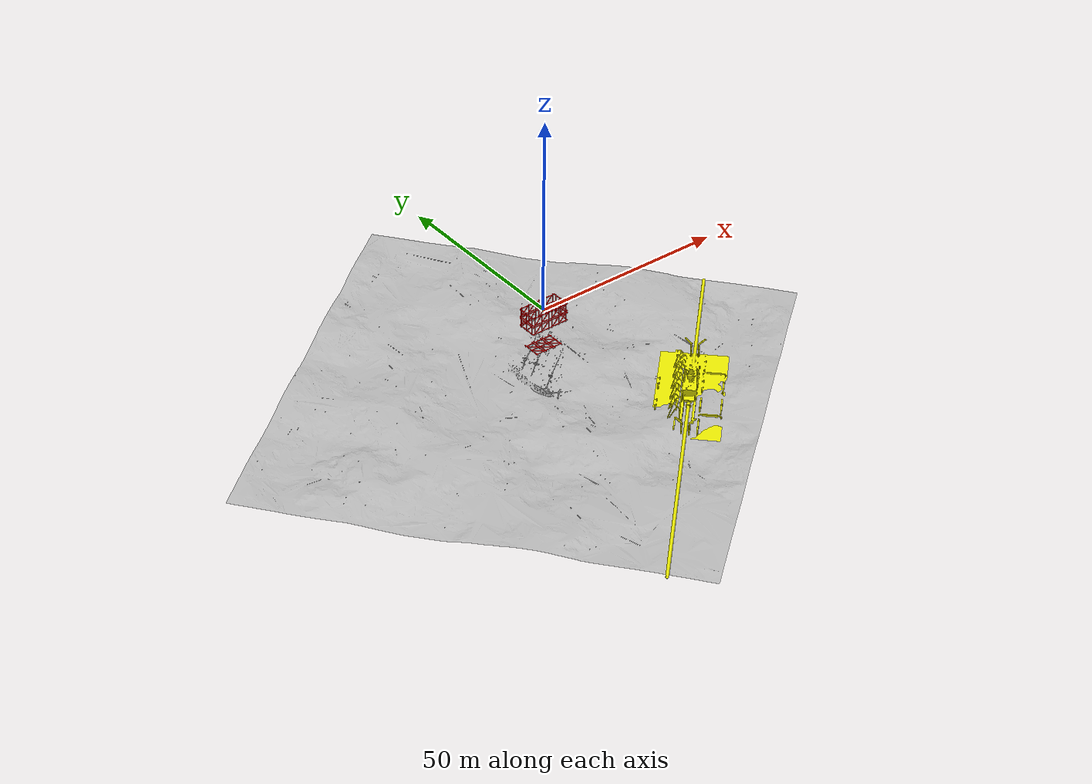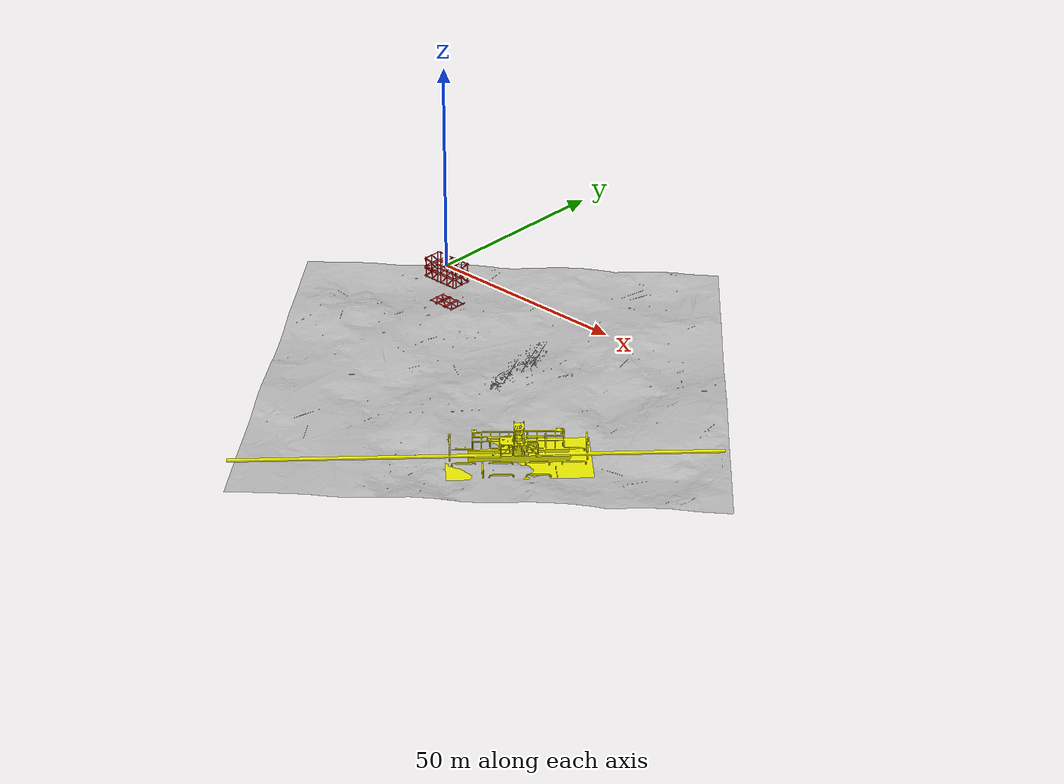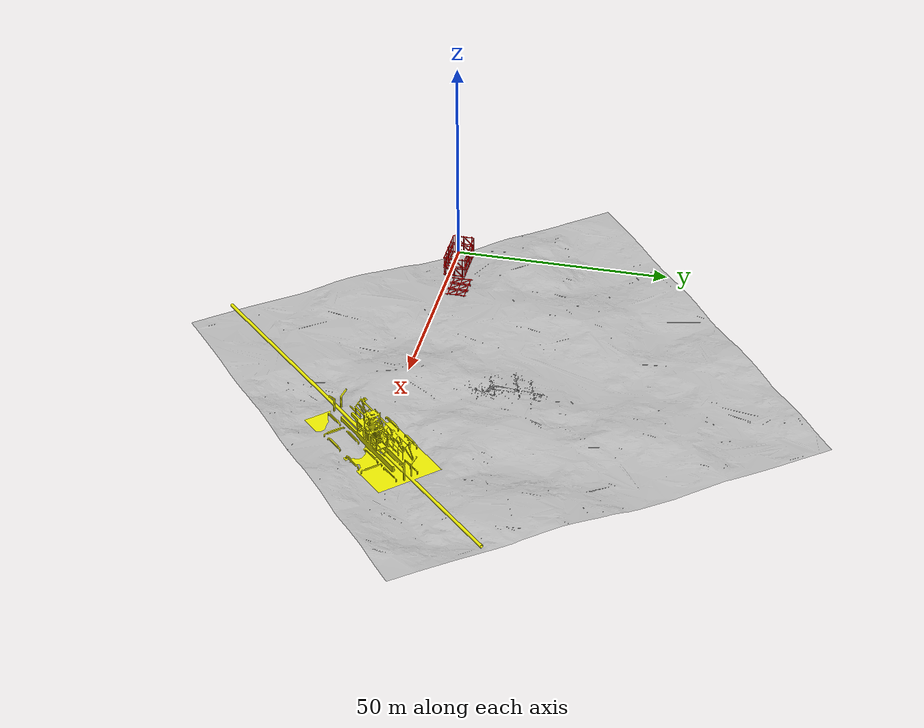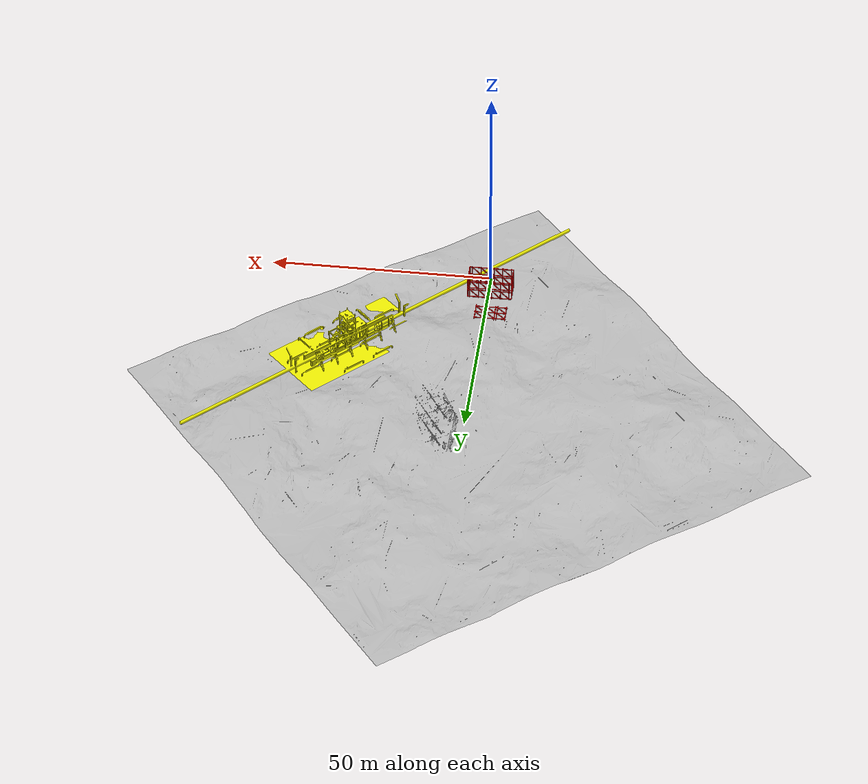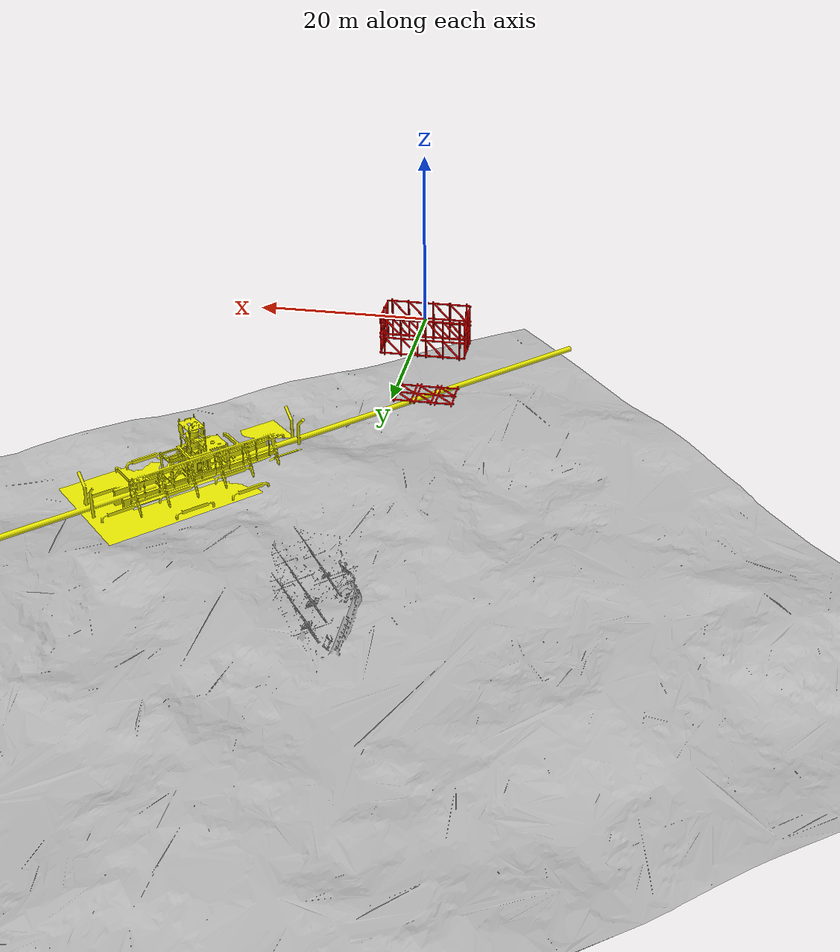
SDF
<?xml version="1.0" ?>
<sdf version="1.4">
    <world name="underwater">
        <include>
            <uri>model://mega_structure</uri>
            <pose>0 0 0 0 0 0</pose>
        </include>

        <include>
            <uri>model://simple_manifold</uri>
            <pose>0 0 -20 0 0 0</pose>
        </include>
    </world>
</sdf>

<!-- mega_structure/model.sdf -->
<sdf version='1.5'>
	<model name='mega_structure'>
		<static>true</static>
        <pose>5 0 0 0 0 0</pose>
		<link name='simple_structure::structure_body_01'>
			<visual name='visual01'>
				<pose>0 0 0 0 0 0</pose>
				<geometry>
					<cylinder>
						<length>2.5</length>
						<radius>0.1</radius>
					</cylinder>
				</geometry>
				<material>
					<ambient>1 0 0 1</ambient>
					<diffuse>1 0 0 1</diffuse>
					<specular>0 0 0 0</specular>
				</material>
			</visual>
			<collision name='collision01'>
				<pose>0 0 0 0 -0 0</pose>
				<geometry>
					<cylinder>
						<length>2.5</length>
						<radius>0.1</radius>
					</cylinder>
				</geometry>
				<max_contacts>10</max_contacts>
				<surface>
					<contact>
						<ode />
					</contact>
					<bounce />
					<friction>
						<ode />
					</friction>
				</surface>
			</collision>
			<visual name='visual02'>
				<pose>0 -2 0 0 -0 0</pose>
				<geometry>
					<cylinder>
						<length>2.5</length>
						<radius>0.1</radius>
					</cylinder>
				</geometry>
				<material>
					<ambient>1 0 0 1</ambient>
					<diffuse>1 0 0 1</diffuse>
					<specular>0 0 0 0</specular>
				</material>
			</visual>
			<collision name='collision02'>
				<pose>0 -2 0 0 -0 0</pose>
				<geometry>
					<cylinder>
						<length>2.5</length>
						<radius>0.1</radius>
					</cylinder>
				</geometry>
				<max_contacts>10</max_contacts>
				<surface>
					<contact>
						<ode />
					</contact>
					<bounce />
					<friction>
						<ode />
					</friction>
				</surface>
			</collision>
			<visual name='visual03'>
				<pose>0 2 0 0 -0 0</pose>
				<geometry>
					<cylinder>
						<length>2.5</length>
						<radius>0.1</radius>
					</cylinder>
				</geometry>
				<material>
					<ambient>1 0 0 1</ambient>
					<diffuse>1 0 0 1</diffuse>
					<specular>0 0 0 0</specular>
				</material>
			</visual>
			<collision name='collision03'>
				<pose>0 2 0 0 -0 0</pose>
				<geometry>
					<cylinder>
						<length>2.5</length>
						<radius>0.1</radius>
					</cylinder>
				</geometry>
				<max_contacts>10</max_contacts>
				<surface>
					<contact>
						<ode />
					</contact>
					<bounce />
					<friction>
						<ode />
					</friction>
				</surface>
			</collision>
			<visual name='visual04'>
				<pose>0 1 0 0.75 -0 0</pose>
				<geometry>
					<cylinder>
						<length>2.5</length>
						<radius>0.1</radius>
					</cylinder>
				</geometry>
				<material>
					<ambient>1 0 0 1</ambient>
					<diffuse>1 0 0 1</diffuse>
					<specular>0 0 0 0</specular>
				</material>
			</visual>
			<collision name='collision04'>
				<pose>0 1 0 0.75 -0 0</pose>
				<geometry>
					<cylinder>
						<length>2.5</length>
						<radius>0.1</radius>
					</cylinder>
				</geometry>
				<max_contacts>10</max_contacts>
				<surface>
					<contact>
						<ode />
					</contact>
					<bounce />
					<friction>
						<ode />
					</friction>
				</surface>
			</collision>
			<visual name='visual05'>
				<pose>0 -1 0 0.75 -0 0</pose>
				<geometry>
					<cylinder>
						<length>2.5</length>
						<radius>0.1</radius>
					</cylinder>
				</geometry>
				<material>
					<ambient>1 0 0 1</ambient>
					<diffuse>1 0 0 1</diffuse>
					<specular>0 0 0 0</specular>
				</material>
			</visual>
			<collision name='collision05'>
				<pose>0 -1 0 0.75 -0 0</pose>
				<geometry>
					<cylinder>
						<length>2.5</length>
						<radius>0.1</radius>
					</cylinder>
				</geometry>
				<max_contacts>10</max_contacts>
				<surface>
					<contact>
						<ode />
					</contact>
					<bounce />
					<friction>
						<ode />
					</friction>
				</surface>
			</collision>
			<visual name='visual06'>
				<pose>0 0 1 1.5707 -0 0</pose>
				<geometry>
					<cylinder>
						<length>5</length>
						<radius>0.1</radius>
					</cylinder>
				</geometry>
				<material>
					<ambient>1 0 0 1</ambient>
					<diffuse>1 0 0 1</diffuse>
					<specular>0 0 0 0</specular>
				</material>
			</visual>
			<collision name='collision06'>
				<pose>0 0 1 1.5707 -0 0</pose>
				<geometry>
					<cylinder>
						<length>2.5</length>
						<radius>0.1</radius>
					</cylinder>
				</geometry>
				<max_contacts>10</max_contacts>
				<surface>
					<contact>
						<ode />
					</contact>
					<bounce />
					<friction>
						<ode />
					</friction>
				</surface>
			</collision>
			<visual name='visual07'>
				<pose>0 0 -1 1.5707 -0 0</pose>
				<geometry>
					<cylinder>
						<length>5</length>
						<radius>0.1</radius>
					</cylinder>
				</geometry>
				<material>
					<ambient>1 0 0 1</ambient>
					<diffuse>1 0 0 1</diffuse>
					<specular>0 0 0 0</specular>
				</material>
			</visual>
			<collision name='collision07'>
				<pose>0 0 -1 1.5707 -0 0</pose>
				<geometry>
					<cylinder>
						<length>2.5</length>
						<radius>0.1</radius>
					</cylinder>
				</geometry>
				<max_contacts>10</max_contacts>
				<surface>
					<contact>
						<ode />
					</contact>
					<bounce />
					<friction>
						<ode />
					</friction>
				</surface>
			</collision>
			<velocity_decay>
				<linear>0</linear>
				<angular>0</angular>
			</velocity_decay>
			<pose>5 0 0 0 -0 0</pose>
			<self_collide>0</self_collide>
			<kinematic>0</kinematic>
			<gravity>1</gravity>
		</link>
		<static>true</static>
		<link name='simple_structure::structure_body_02'>
			<visual name='visual01'>
				<pose>0 0 0 0 -0 0</pose>
				<geometry>
					<cylinder>
						<length>2.5</length>
						<radius>0.1</radius>
					</cylinder>
				</geometry>
				<material>
					<ambient>1 0 0 1</ambient>
					<diffuse>1 0 0 1</diffuse>
					<specular>0 0 0 0</specular>
				</material>
			</visual>
			<collision name='collision01'>
				<pose>0 0 0 0 -0 0</pose>
				<geometry>
					<cylinder>
						<length>2.5</length>
						<radius>0.1</radius>
					</cylinder>
				</geometry>
				<max_contacts>10</max_contacts>
				<surface>
					<contact>
						<ode />
					</contact>
					<bounce />
					<friction>
						<ode />
					</friction>
				</surface>
			</collision>
			<visual name='visual02'>
				<pose>0 -2 0 0 -0 0</pose>
				<geometry>
					<cylinder>
						<length>2.5</length>
						<radius>0.1</radius>
					</cylinder>
				</geometry>
				<material>
					<ambient>1 0 0 1</ambient>
					<diffuse>1 0 0 1</diffuse>
					<specular>0 0 0 0</specular>
				</material>
			</visual>
			<collision name='collision02'>
				<pose>0 -2 0 0 -0 0</pose>
				<geometry>
					<cylinder>
						<length>2.5</length>
						<radius>0.1</radius>
					</cylinder>
				</geometry>
				<max_contacts>10</max_contacts>
				<surface>
					<contact>
						<ode />
					</contact>
					<bounce />
					<friction>
						<ode />
					</friction>
				</surface>
			</collision>
			<visual name='visual03'>
				<pose>0 2 0 0 -0 0</pose>
				<geometry>
					<cylinder>
						<length>2.5</length>
						<radius>0.1</radius>
					</cylinder>
				</geometry>
				<material>
					<ambient>1 0 0 1</ambient>
					<diffuse>1 0 0 1</diffuse>
					<specular>0 0 0 0</specular>
				</material>
			</visual>
			<collision name='collision03'>
				<pose>0 2 0 0 -0 0</pose>
				<geometry>
					<cylinder>
						<length>2.5</length>
						<radius>0.1</radius>
					</cylinder>
				</geometry>
				<max_contacts>10</max_contacts>
				<surface>
					<contact>
						<ode />
					</contact>
					<bounce />
					<friction>
						<ode />
					</friction>
				</surface>
			</collision>
			<visual name='visual04'>
				<pose>0 1 0 0.75 -0 0</pose>
				<geometry>
					<cylinder>
						<length>2.5</length>
						<radius>0.1</radius>
					</cylinder>
				</geometry>
				<material>
					<ambient>1 0 0 1</ambient>
					<diffuse>1 0 0 1</diffuse>
					<specular>0 0 0 0</specular>
				</material>
			</visual>
			<collision name='collision04'>
				<pose>0 1 0 0.75 -0 0</pose>
				<geometry>
					<cylinder>
						<length>2.5</length>
						<radius>0.1</radius>
					</cylinder>
				</geometry>
				<max_contacts>10</max_contacts>
				<surface>
					<contact>
						<ode />
					</contact>
					<bounce />
					<friction>
						<ode />
					</friction>
				</surface>
			</collision>
			<visual name='visual05'>
				<pose>0 -1 0 0.75 -0 0</pose>
				<geometry>
					<cylinder>
						<length>2.5</length>
						<radius>0.1</radius>
					</cylinder>
				</geometry>
				<material>
					<ambient>1 0 0 1</ambient>
					<diffuse>1 0 0 1</diffuse>
					<specular>0 0 0 0</specular>
				</material>
			</visual>
			<collision name='collision05'>
				<pose>0 -1 0 0.75 -0 0</pose>
				<geometry>
					<cylinder>
						<length>2.5</length>
						<radius>0.1</radius>
					</cylinder>
				</geometry>
				<max_contacts>10</max_contacts>
				<surface>
					<contact>
						<ode />
					</contact>
					<bounce />
					<friction>
						<ode />
					</friction>
				</surface>
			</collision>
			<visual name='visual06'>
				<pose>0 0 1 1.5707 -0 0</pose>
				<geometry>
					<cylinder>
						<length>5</length>
						<radius>0.1</radius>
					</cylinder>
				</geometry>
				<material>
					<ambient>1 0 0 1</ambient>
					<diffuse>1 0 0 1</diffuse>
					<specular>0 0 0 0</specular>
				</material>
			</visual>
			<collision name='collision06'>
				<pose>0 0 1 1.5707 -0 0</pose>
				<geometry>
					<cylinder>
						<length>2.5</length>
						<radius>0.1</radius>
					</cylinder>
				</geometry>
				<max_contacts>10</max_contacts>
				<surface>
					<contact>
						<ode />
					</contact>
					<bounce />
					<friction>
						<ode />
					</friction>
				</surface>
			</collision>
			<visual name='visual07'>
				<pose>0 0 -1 1.5707 -0 0</pose>
				<geometry>
					<cylinder>
						<length>5</length>
						<radius>0.1</radius>
					</cylinder>
				</geometry>
				<material>
					<ambient>1 0 0 1</ambient>
					<diffuse>1 0 0 1</diffuse>
					<specular>0 0 0 0</specular>
				</material>
			</visual>
			<collision name='collision07'>
				<pose>0 0 -1 1.5707 -0 0</pose>
				<geometry>
					<cylinder>
						<length>2.5</length>
						<radius>0.1</radius>
					</cylinder>
				</geometry>
				<max_contacts>10</max_contacts>
				<surface>
					<contact>
						<ode />
					</contact>
					<bounce />
					<friction>
						<ode />
					</friction>
				</surface>
			</collision>
			<velocity_decay>
				<linear>0</linear>
				<angular>0</angular>
			</velocity_decay>
			<pose>-5 0 0 0 -0 0</pose>
			<self_collide>0</self_collide>
			<kinematic>0</kinematic>
			<gravity>1</gravity>
		</link>
		<static>true</static>
		<link name='simple_structure::structure_body_03'>
			<visual name='visual01'>
				<pose>0 0 0 0 -0 0</pose>
				<geometry>
					<cylinder>
						<length>2.5</length>
						<radius>0.1</radius>
					</cylinder>
				</geometry>
				<material>
					<ambient>1 0 0 1</ambient>
					<diffuse>1 0 0 1</diffuse>
					<specular>0 0 0 0</specular>
				</material>
			</visual>
			<collision name='collision01'>
				<pose>0 0 0 0 -0 0</pose>
				<geometry>
					<cylinder>
						<length>2.5</length>
						<radius>0.1</radius>
					</cylinder>
				</geometry>
				<max_contacts>10</max_contacts>
				<surface>
					<contact>
						<ode />
					</contact>
					<bounce />
					<friction>
						<ode />
					</friction>
				</surface>
			</collision>
			<visual name='visual02'>
				<pose>0 -2 0 0 -0 0</pose>
				<geometry>
					<cylinder>
						<length>2.5</length>
						<radius>0.1</radius>
					</cylinder>
				</geometry>
				<material>
					<ambient>1 0 0 1</ambient>
					<diffuse>1 0 0 1</diffuse>
					<specular>0 0 0 0</specular>
				</material>
			</visual>
			<collision name='collision02'>
				<pose>0 -2 0 0 -0 0</pose>
				<geometry>
					<cylinder>
						<length>2.5</length>
						<radius>0.1</radius>
					</cylinder>
				</geometry>
				<max_contacts>10</max_contacts>
				<surface>
					<contact>
						<ode />
					</contact>
					<bounce />
					<friction>
						<ode />
					</friction>
				</surface>
			</collision>
			<visual name='visual03'>
				<pose>0 2 0 0 -0 0</pose>
				<geometry>
					<cylinder>
						<length>2.5</length>
						<radius>0.1</radius>
					</cylinder>
				</geometry>
				<material>
					<ambient>1 0 0 1</ambient>
					<diffuse>1 0 0 1</diffuse>
					<specular>0 0 0 0</specular>
				</material>
			</visual>
			<collision name='collision03'>
				<pose>0 2 0 0 -0 0</pose>
				<geometry>
					<cylinder>
						<length>2.5</length>
						<radius>0.1</radius>
					</cylinder>
				</geometry>
				<max_contacts>10</max_contacts>
				<surface>
					<contact>
						<ode />
					</contact>
					<bounce />
					<friction>
						<ode />
					</friction>
				</surface>
			</collision>
			<visual name='visual04'>
				<pose>0 1 0 0.75 -0 0</pose>
				<geometry>
					<cylinder>
						<length>2.5</length>
						<radius>0.1</radius>
					</cylinder>
				</geometry>
				<material>
					<ambient>1 0 0 1</ambient>
					<diffuse>1 0 0 1</diffuse>
					<specular>0 0 0 0</specular>
				</material>
			</visual>
			<collision name='collision04'>
				<pose>0 1 0 0.75 -0 0</pose>
				<geometry>
					<cylinder>
						<length>2.5</length>
						<radius>0.1</radius>
					</cylinder>
				</geometry>
				<max_contacts>10</max_contacts>
				<surface>
					<contact>
						<ode />
					</contact>
					<bounce />
					<friction>
						<ode />
					</friction>
				</surface>
			</collision>
			<visual name='visual05'>
				<pose>0 -1 0 0.75 -0 0</pose>
				<geometry>
					<cylinder>
						<length>2.5</length>
						<radius>0.1</radius>
					</cylinder>
				</geometry>
				<material>
					<ambient>1 0 0 1</ambient>
					<diffuse>1 0 0 1</diffuse>
					<specular>0 0 0 0</specular>
				</material>
			</visual>
			<collision name='collision05'>
				<pose>0 -1 0 0.75 -0 0</pose>
				<geometry>
					<cylinder>
						<length>2.5</length>
						<radius>0.1</radius>
					</cylinder>
				</geometry>
				<max_contacts>10</max_contacts>
				<surface>
					<contact>
						<ode />
					</contact>
					<bounce />
					<friction>
						<ode />
					</friction>
				</surface>
			</collision>
			<visual name='visual06'>
				<pose>0 0 1 1.5707 -0 0</pose>
				<geometry>
					<cylinder>
						<length>5</length>
						<radius>0.1</radius>
					</cylinder>
				</geometry>
				<material>
					<ambient>1 0 0 1</ambient>
					<diffuse>1 0 0 1</diffuse>
					<specular>0 0 0 0</specular>
				</material>
			</visual>
			<collision name='collision06'>
				<pose>0 0 1 1.5707 -0 0</pose>
				<geometry>
					<cylinder>
						<length>2.5</length>
						<radius>0.1</radius>
					</cylinder>
				</geometry>
				<max_contacts>10</max_contacts>
				<surface>
					<contact>
						<ode />
					</contact>
					<bounce />
					<friction>
						<ode />
					</friction>
				</surface>
			</collision>
			<visual name='visual07'>
				<pose>0 0 -1 1.5707 -0 0</pose>
				<geometry>
					<cylinder>
						<length>5</length>
						<radius>0.1</radius>
					</cylinder>
				</geometry>
				<material>
					<ambient>1 0 0 1</ambient>
					<diffuse>1 0 0 1</diffuse>
					<specular>0 0 0 0</specular>
				</material>
			</visual>
			<collision name='collision07'>
				<pose>0 0 -1 1.5707 -0 0</pose>
				<geometry>
					<cylinder>
						<length>2.5</length>
						<radius>0.1</radius>
					</cylinder>
				</geometry>
				<max_contacts>10</max_contacts>
				<surface>
					<contact>
						<ode />
					</contact>
					<bounce />
					<friction>
						<ode />
					</friction>
				</surface>
			</collision>
			<velocity_decay>
				<linear>0</linear>
				<angular>0</angular>
			</velocity_decay>
			<pose>2.5 2.5 0 0 -0 1.5707</pose>
			<self_collide>0</self_collide>
			<kinematic>0</kinematic>
			<gravity>1</gravity>
		</link>
		<static>true</static>
		<link name='simple_structure::structure_body_04'>
			<visual name='visual01'>
				<pose>0 0 0 0 -0 0</pose>
				<geometry>
					<cylinder>
						<length>2.5</length>
						<radius>0.1</radius>
					</cylinder>
				</geometry>
				<material>
					<ambient>1 0 0 1</ambient>
					<diffuse>1 0 0 1</diffuse>
					<specular>0 0 0 0</specular>
				</material>
			</visual>
			<collision name='collision01'>
				<pose>0 0 0 0 -0 0</pose>
				<geometry>
					<cylinder>
						<length>2.5</length>
						<radius>0.1</radius>
					</cylinder>
				</geometry>
				<max_contacts>10</max_contacts>
				<surface>
					<contact>
						<ode />
					</contact>
					<bounce />
					<friction>
						<ode />
					</friction>
				</surface>
			</collision>
			<visual name='visual02'>
				<pose>0 -2 0 0 -0 0</pose>
				<geometry>
					<cylinder>
						<length>2.5</length>
						<radius>0.1</radius>
					</cylinder>
				</geometry>
				<material>
					<ambient>1 0 0 1</ambient>
					<diffuse>1 0 0 1</diffuse>
					<specular>0 0 0 0</specular>
				</material>
			</visual>
			<collision name='collision02'>
				<pose>0 -2 0 0 -0 0</pose>
				<geometry>
					<cylinder>
						<length>2.5</length>
						<radius>0.1</radius>
					</cylinder>
				</geometry>
				<max_contacts>10</max_contacts>
				<surface>
					<contact>
						<ode />
					</contact>
					<bounce />
					<friction>
						<ode />
					</friction>
				</surface>
			</collision>
			<visual name='visual03'>
				<pose>0 2 0 0 -0 0</pose>
				<geometry>
					<cylinder>
						<length>2.5</length>
						<radius>0.1</radius>
					</cylinder>
				</geometry>
				<material>
					<ambient>1 0 0 1</ambient>
					<diffuse>1 0 0 1</diffuse>
					<specular>0 0 0 0</specular>
				</material>
			</visual>
			<collision name='collision03'>
				<pose>0 2 0 0 -0 0</pose>
				<geometry>
					<cylinder>
						<length>2.5</length>
						<radius>0.1</radius>
					</cylinder>
				</geometry>
				<max_contacts>10</max_contacts>
				<surface>
					<contact>
						<ode />
					</contact>
					<bounce />
					<friction>
						<ode />
					</friction>
				</surface>
			</collision>
			<visual name='visual04'>
				<pose>0 1 0 0.75 -0 0</pose>
				<geometry>
					<cylinder>
						<length>2.5</length>
						<radius>0.1</radius>
					</cylinder>
				</geometry>
				<material>
					<ambient>1 0 0 1</ambient>
					<diffuse>1 0 0 1</diffuse>
					<specular>0 0 0 0</specular>
				</material>
			</visual>
			<collision name='collision04'>
				<pose>0 1 0 0.75 -0 0</pose>
				<geometry>
					<cylinder>
						<length>2.5</length>
						<radius>0.1</radius>
					</cylinder>
				</geometry>
				<max_contacts>10</max_contacts>
				<surface>
					<contact>
						<ode />
					</contact>
					<bounce />
					<friction>
						<ode />
					</friction>
				</surface>
			</collision>
			<visual name='visual05'>
				<pose>0 -1 0 0.75 -0 0</pose>
				<geometry>
					<cylinder>
						<length>2.5</length>
						<radius>0.1</radius>
					</cylinder>
				</geometry>
				<material>
					<ambient>1 0 0 1</ambient>
					<diffuse>1 0 0 1</diffuse>
					<specular>0 0 0 0</specular>
				</material>
			</visual>
			<collision name='collision05'>
				<pose>0 -1 0 0.75 -0 0</pose>
				<geometry>
					<cylinder>
						<length>2.5</length>
						<radius>0.1</radius>
					</cylinder>
				</geometry>
				<max_contacts>10</max_contacts>
				<surface>
					<contact>
						<ode />
					</contact>
					<bounce />
					<friction>
						<ode />
					</friction>
				</surface>
			</collision>
			<visual name='visual06'>
				<pose>0 0 1 1.5707 -0 0</pose>
				<geometry>
					<cylinder>
						<length>5</length>
						<radius>0.1</radius>
					</cylinder>
				</geometry>
				<material>
					<ambient>1 0 0 1</ambient>
					<diffuse>1 0 0 1</diffuse>
					<specular>0 0 0 0</specular>
				</material>
			</visual>
			<collision name='collision06'>
				<pose>0 0 1 1.5707 -0 0</pose>
				<geometry>
					<cylinder>
						<length>2.5</length>
						<radius>0.1</radius>
					</cylinder>
				</geometry>
				<max_contacts>10</max_contacts>
				<surface>
					<contact>
						<ode />
					</contact>
					<bounce />
					<friction>
						<ode />
					</friction>
				</surface>
			</collision>
			<visual name='visual07'>
				<pose>0 0 -1 1.5707 -0 0</pose>
				<geometry>
					<cylinder>
						<length>5</length>
						<radius>0.1</radius>
					</cylinder>
				</geometry>
				<material>
					<ambient>1 0 0 1</ambient>
					<diffuse>1 0 0 1</diffuse>
					<specular>0 0 0 0</specular>
				</material>
			</visual>
			<collision name='collision07'>
				<pose>0 0 -1 1.5707 -0 0</pose>
				<geometry>
					<cylinder>
						<length>2.5</length>
						<radius>0.1</radius>
					</cylinder>
				</geometry>
				<max_contacts>10</max_contacts>
				<surface>
					<contact>
						<ode />
					</contact>
					<bounce />
					<friction>
						<ode />
					</friction>
				</surface>
			</collision>
			<velocity_decay>
				<linear>0</linear>
				<angular>0</angular>
			</velocity_decay>
			<pose>-2.5 2.5 0 0 -0 1.5707</pose>
			<self_collide>0</self_collide>
			<kinematic>0</kinematic>
			<gravity>1</gravity>
		</link>
		<static>true</static>
		<link name='simple_structure::structure_body_05'>
			<visual name='visual01'>
				<pose>0 0 0 0 -0 0</pose>
				<geometry>
					<cylinder>
						<length>2.5</length>
						<radius>0.1</radius>
					</cylinder>
				</geometry>
				<material>
					<ambient>1 0 0 1</ambient>
					<diffuse>1 0 0 1</diffuse>
					<specular>0 0 0 0</specular>
				</material>
			</visual>
			<collision name='collision01'>
				<pose>0 0 0 0 -0 0</pose>
				<geometry>
					<cylinder>
						<length>2.5</length>
						<radius>0.1</radius>
					</cylinder>
				</geometry>
				<max_contacts>10</max_contacts>
				<surface>
					<contact>
						<ode />
					</contact>
					<bounce />
					<friction>
						<ode />
					</friction>
				</surface>
			</collision>
			<visual name='visual02'>
				<pose>0 -2 0 0 -0 0</pose>
				<geometry>
					<cylinder>
						<length>2.5</length>
						<radius>0.1</radius>
					</cylinder>
				</geometry>
				<material>
					<ambient>1 0 0 1</ambient>
					<diffuse>1 0 0 1</diffuse>
					<specular>0 0 0 0</specular>
				</material>
			</visual>
			<collision name='collision02'>
				<pose>0 -2 0 0 -0 0</pose>
				<geometry>
					<cylinder>
						<length>2.5</length>
						<radius>0.1</radius>
					</cylinder>
				</geometry>
				<max_contacts>10</max_contacts>
				<surface>
					<contact>
						<ode />
					</contact>
					<bounce />
					<friction>
						<ode />
					</friction>
				</surface>
			</collision>
			<visual name='visual03'>
				<pose>0 2 0 0 -0 0</pose>
				<geometry>
					<cylinder>
						<length>2.5</length>
						<radius>0.1</radius>
					</cylinder>
				</geometry>
				<material>
					<ambient>1 0 0 1</ambient>
					<diffuse>1 0 0 1</diffuse>
					<specular>0 0 0 0</specular>
				</material>
			</visual>
			<collision name='collision03'>
				<pose>0 2 0 0 -0 0</pose>
				<geometry>
					<cylinder>
						<length>2.5</length>
						<radius>0.1</radius>
					</cylinder>
				</geometry>
				<max_contacts>10</max_contacts>
				<surface>
					<contact>
						<ode />
					</contact>
					<bounce />
					<friction>
						<ode />
					</friction>
				</surface>
			</collision>
			<visual name='visual04'>
				<pose>0 1 0 0.75 -0 0</pose>
				<geometry>
					<cylinder>
						<length>2.5</length>
						<radius>0.1</radius>
					</cylinder>
				</geometry>
				<material>
					<ambient>1 0 0 1</ambient>
					<diffuse>1 0 0 1</diffuse>
					<specular>0 0 0 0</specular>
				</material>
			</visual>
			<collision name='collision04'>
				<pose>0 1 0 0.75 -0 0</pose>
				<geometry>
					<cylinder>
						<length>2.5</length>
						<radius>0.1</radius>
					</cylinder>
				</geometry>
				<max_contacts>10</max_contacts>
				<surface>
					<contact>
						<ode />
					</contact>
					<bounce />
					<friction>
						<ode />
					</friction>
				</surface>
			</collision>
			<visual name='visual05'>
				<pose>0 -1 0 0.75 -0 0</pose>
				<geometry>
					<cylinder>
						<length>2.5</length>
						<radius>0.1</radius>
					</cylinder>
				</geometry>
				<material>
					<ambient>1 0 0 1</ambient>
					<diffuse>1 0 0 1</diffuse>
					<specular>0 0 0 0</specular>
				</material>
			</visual>
			<collision name='collision05'>
				<pose>0 -1 0 0.75 -0 0</pose>
				<geometry>
					<cylinder>
						<length>2.5</length>
						<radius>0.1</radius>
					</cylinder>
				</geometry>
				<max_contacts>10</max_contacts>
				<surface>
					<contact>
						<ode />
					</contact>
					<bounce />
					<friction>
						<ode />
					</friction>
				</surface>
			</collision>
			<visual name='visual06'>
				<pose>0 0 1 1.5707 -0 0</pose>
				<geometry>
					<cylinder>
						<length>5</length>
						<radius>0.1</radius>
					</cylinder>
				</geometry>
				<material>
					<ambient>1 0 0 1</ambient>
					<diffuse>1 0 0 1</diffuse>
					<specular>0 0 0 0</specular>
				</material>
			</visual>
			<collision name='collision06'>
				<pose>0 0 1 1.5707 -0 0</pose>
				<geometry>
					<cylinder>
						<length>2.5</length>
						<radius>0.1</radius>
					</cylinder>
				</geometry>
				<max_contacts>10</max_contacts>
				<surface>
					<contact>
						<ode />
					</contact>
					<bounce />
					<friction>
						<ode />
					</friction>
				</surface>
			</collision>
			<visual name='visual07'>
				<pose>0 0 -1 1.5707 -0 0</pose>
				<geometry>
					<cylinder>
						<length>5</length>
						<radius>0.1</radius>
					</cylinder>
				</geometry>
				<material>
					<ambient>1 0 0 1</ambient>
					<diffuse>1 0 0 1</diffuse>
					<specular>0 0 0 0</specular>
				</material>
			</visual>
			<collision name='collision07'>
				<pose>0 0 -1 1.5707 -0 0</pose>
				<geometry>
					<cylinder>
						<length>2.5</length>
						<radius>0.1</radius>
					</cylinder>
				</geometry>
				<max_contacts>10</max_contacts>
				<surface>
					<contact>
						<ode />
					</contact>
					<bounce />
					<friction>
						<ode />
					</friction>
				</surface>
			</collision>
			<velocity_decay>
				<linear>0</linear>
				<angular>0</angular>
			</velocity_decay>
			<pose>2.5 -2.5 0 0 -0 1.5707</pose>
			<self_collide>0</self_collide>
			<kinematic>0</kinematic>
			<gravity>1</gravity>
		</link>
		<static>true</static>
		<link name='simple_structure::structure_body_06'>
			<visual name='visual01'>
				<pose>0 0 0 0 -0 0</pose>
				<geometry>
					<cylinder>
						<length>2.5</length>
						<radius>0.1</radius>
					</cylinder>
				</geometry>
				<material>
					<ambient>1 0 0 1</ambient>
					<diffuse>1 0 0 1</diffuse>
					<specular>0 0 0 0</specular>
				</material>
			</visual>
			<collision name='collision01'>
				<pose>0 0 0 0 -0 0</pose>
				<geometry>
					<cylinder>
						<length>2.5</length>
						<radius>0.1</radius>
					</cylinder>
				</geometry>
				<max_contacts>10</max_contacts>
				<surface>
					<contact>
						<ode />
					</contact>
					<bounce />
					<friction>
						<ode />
					</friction>
				</surface>
			</collision>
			<visual name='visual02'>
				<pose>0 -2 0 0 -0 0</pose>
				<geometry>
					<cylinder>
						<length>2.5</length>
						<radius>0.1</radius>
					</cylinder>
				</geometry>
				<material>
					<ambient>1 0 0 1</ambient>
					<diffuse>1 0 0 1</diffuse>
					<specular>0 0 0 0</specular>
				</material>
			</visual>
			<collision name='collision02'>
				<pose>0 -2 0 0 -0 0</pose>
				<geometry>
					<cylinder>
						<length>2.5</length>
						<radius>0.1</radius>
					</cylinder>
				</geometry>
				<max_contacts>10</max_contacts>
				<surface>
					<contact>
						<ode />
					</contact>
					<bounce />
					<friction>
						<ode />
					</friction>
				</surface>
			</collision>
			<visual name='visual03'>
				<pose>0 2 0 0 -0 0</pose>
				<geometry>
					<cylinder>
						<length>2.5</length>
						<radius>0.1</radius>
					</cylinder>
				</geometry>
				<material>
					<ambient>1 0 0 1</ambient>
					<diffuse>1 0 0 1</diffuse>
					<specular>0 0 0 0</specular>
				</material>
			</visual>
			<collision name='collision03'>
				<pose>0 2 0 0 -0 0</pose>
				<geometry>
					<cylinder>
						<length>2.5</length>
						<radius>0.1</radius>
					</cylinder>
				</geometry>
				<max_contacts>10</max_contacts>
				<surface>
					<contact>
						<ode />
					</contact>
					<bounce />
					<friction>
						<ode />
					</friction>
				</surface>
			</collision>
			<visual name='visual04'>
				<pose>0 1 0 0.75 -0 0</pose>
				<geometry>
					<cylinder>
						<length>2.5</length>
						<radius>0.1</radius>
					</cylinder>
				</geometry>
				<material>
					<ambient>1 0 0 1</ambient>
					<diffuse>1 0 0 1</diffuse>
					<specular>0 0 0 0</specular>
				</material>
			</visual>
			<collision name='collision04'>
				<pose>0 1 0 0.75 -0 0</pose>
				<geometry>
					<cylinder>
						<length>2.5</length>
						<radius>0.1</radius>
					</cylinder>
				</geometry>
				<max_contacts>10</max_contacts>
				<surface>
					<contact>
						<ode />
					</contact>
					<bounce />
					<friction>
						<ode />
					</friction>
				</surface>
			</collision>
			<visual name='visual05'>
				<pose>0 -1 0 0.75 -0 0</pose>
				<geometry>
					<cylinder>
						<length>2.5</length>
						<radius>0.1</radius>
					</cylinder>
				</geometry>
				<material>
					<ambient>1 0 0 1</ambient>
					<diffuse>1 0 0 1</diffuse>
					<specular>0 0 0 0</specular>
				</material>
			</visual>
			<collision name='collision05'>
				<pose>0 -1 0 0.75 -0 0</pose>
				<geometry>
					<cylinder>
						<length>2.5</length>
						<radius>0.1</radius>
					</cylinder>
				</geometry>
				<max_contacts>10</max_contacts>
				<surface>
					<contact>
						<ode />
					</contact>
					<bounce />
					<friction>
						<ode />
					</friction>
				</surface>
			</collision>
			<visual name='visual06'>
				<pose>0 0 1 1.5707 -0 0</pose>
				<geometry>
					<cylinder>
						<length>5</length>
						<radius>0.1</radius>
					</cylinder>
				</geometry>
				<material>
					<ambient>1 0 0 1</ambient>
					<diffuse>1 0 0 1</diffuse>
					<specular>0 0 0 0</specular>
				</material>
			</visual>
			<collision name='collision06'>
				<pose>0 0 1 1.5707 -0 0</pose>
				<geometry>
					<cylinder>
						<length>2.5</length>
						<radius>0.1</radius>
					</cylinder>
				</geometry>
				<max_contacts>10</max_contacts>
				<surface>
					<contact>
						<ode />
					</contact>
					<bounce />
					<friction>
						<ode />
					</friction>
				</surface>
			</collision>
			<visual name='visual07'>
				<pose>0 0 -1 1.5707 -0 0</pose>
				<geometry>
					<cylinder>
						<length>5</length>
						<radius>0.1</radius>
					</cylinder>
				</geometry>
				<material>
					<ambient>1 0 0 1</ambient>
					<diffuse>1 0 0 1</diffuse>
					<specular>0 0 0 0</specular>
				</material>
			</visual>
			<collision name='collision07'>
				<pose>0 0 -1 1.5707 -0 0</pose>
				<geometry>
					<cylinder>
						<length>2.5</length>
						<radius>0.1</radius>
					</cylinder>
				</geometry>
				<max_contacts>10</max_contacts>
				<surface>
					<contact>
						<ode />
					</contact>
					<bounce />
					<friction>
						<ode />
					</friction>
				</surface>
			</collision>
			<velocity_decay>
				<linear>0</linear>
				<angular>0</angular>
			</velocity_decay>
			<pose>-2.5 -2.5 0 0 -0 1.5707</pose>
			<self_collide>0</self_collide>
			<kinematic>0</kinematic>
			<gravity>1</gravity>
		</link>
		<static>true</static>
		<link name='simple_structure::structure_body_07'>
			<visual name='visual01'>
				<pose>0 0 0 0 -0 0</pose>
				<geometry>
					<cylinder>
						<length>2.5</length>
						<radius>0.1</radius>
					</cylinder>
				</geometry>
				<material>
					<ambient>1 0 0 1</ambient>
					<diffuse>1 0 0 1</diffuse>
					<specular>0 0 0 0</specular>
				</material>
			</visual>
			<collision name='collision01'>
				<pose>0 0 0 0 -0 0</pose>
				<geometry>
					<cylinder>
						<length>2.5</length>
						<radius>0.1</radius>
					</cylinder>
				</geometry>
				<max_contacts>10</max_contacts>
				<surface>
					<contact>
						<ode />
					</contact>
					<bounce />
					<friction>
						<ode />
					</friction>
				</surface>
			</collision>
			<visual name='visual02'>
				<pose>0 -2 0 0 -0 0</pose>
				<geometry>
					<cylinder>
						<length>2.5</length>
						<radius>0.1</radius>
					</cylinder>
				</geometry>
				<material>
					<ambient>1 0 0 1</ambient>
					<diffuse>1 0 0 1</diffuse>
					<specular>0 0 0 0</specular>
				</material>
			</visual>
			<collision name='collision02'>
				<pose>0 -2 0 0 -0 0</pose>
				<geometry>
					<cylinder>
						<length>2.5</length>
						<radius>0.1</radius>
					</cylinder>
				</geometry>
				<max_contacts>10</max_contacts>
				<surface>
					<contact>
						<ode />
					</contact>
					<bounce />
					<friction>
						<ode />
					</friction>
				</surface>
			</collision>
			<visual name='visual03'>
				<pose>0 2 0 0 -0 0</pose>
				<geometry>
					<cylinder>
						<length>2.5</length>
						<radius>0.1</radius>
					</cylinder>
				</geometry>
				<material>
					<ambient>1 0 0 1</ambient>
					<diffuse>1 0 0 1</diffuse>
					<specular>0 0 0 0</specular>
				</material>
			</visual>
			<collision name='collision03'>
				<pose>0 2 0 0 -0 0</pose>
				<geometry>
					<cylinder>
						<length>2.5</length>
						<radius>0.1</radius>
					</cylinder>
				</geometry>
				<max_contacts>10</max_contacts>
				<surface>
					<contact>
						<ode />
					</contact>
					<bounce />
					<friction>
						<ode />
					</friction>
				</surface>
			</collision>
			<visual name='visual04'>
				<pose>0 1 0 0.75 -0 0</pose>
				<geometry>
					<cylinder>
						<length>2.5</length>
						<radius>0.1</radius>
					</cylinder>
				</geometry>
				<material>
					<ambient>1 0 0 1</ambient>
					<diffuse>1 0 0 1</diffuse>
					<specular>0 0 0 0</specular>
				</material>
			</visual>
			<collision name='collision04'>
				<pose>0 1 0 0.75 -0 0</pose>
				<geometry>
					<cylinder>
						<length>2.5</length>
						<radius>0.1</radius>
					</cylinder>
				</geometry>
				<max_contacts>10</max_contacts>
				<surface>
					<contact>
						<ode />
					</contact>
					<bounce />
					<friction>
						<ode />
					</friction>
				</surface>
			</collision>
			<visual name='visual05'>
				<pose>0 -1 0 0.75 -0 0</pose>
				<geometry>
					<cylinder>
						<length>2.5</length>
						<radius>0.1</radius>
					</cylinder>
				</geometry>
				<material>
					<ambient>1 0 0 1</ambient>
					<diffuse>1 0 0 1</diffuse>
					<specular>0 0 0 0</specular>
				</material>
			</visual>
			<collision name='collision05'>
				<pose>0 -1 0 0.75 -0 0</pose>
				<geometry>
					<cylinder>
						<length>2.5</length>
						<radius>0.1</radius>
					</cylinder>
				</geometry>
				<max_contacts>10</max_contacts>
				<surface>
					<contact>
						<ode />
					</contact>
					<bounce />
					<friction>
						<ode />
					</friction>
				</surface>
			</collision>
			<visual name='visual06'>
				<pose>0 0 1 1.5707 -0 0</pose>
				<geometry>
					<cylinder>
						<length>5</length>
						<radius>0.1</radius>
					</cylinder>
				</geometry>
				<material>
					<ambient>1 0 0 1</ambient>
					<diffuse>1 0 0 1</diffuse>
					<specular>0 0 0 0</specular>
				</material>
			</visual>
			<collision name='collision06'>
				<pose>0 0 1 1.5707 -0 0</pose>
				<geometry>
					<cylinder>
						<length>2.5</length>
						<radius>0.1</radius>
					</cylinder>
				</geometry>
				<max_contacts>10</max_contacts>
				<surface>
					<contact>
						<ode />
					</contact>
					<bounce />
					<friction>
						<ode />
					</friction>
				</surface>
			</collision>
			<visual name='visual07'>
				<pose>0 0 -1 1.5707 -0 0</pose>
				<geometry>
					<cylinder>
						<length>5</length>
						<radius>0.1</radius>
					</cylinder>
				</geometry>
				<material>
					<ambient>1 0 0 1</ambient>
					<diffuse>1 0 0 1</diffuse>
					<specular>0 0 0 0</specular>
				</material>
			</visual>
			<collision name='collision07'>
				<pose>0 0 -1 1.5707 -0 0</pose>
				<geometry>
					<cylinder>
						<length>2.5</length>
						<radius>0.1</radius>
					</cylinder>
				</geometry>
				<max_contacts>10</max_contacts>
				<surface>
					<contact>
						<ode />
					</contact>
					<bounce />
					<friction>
						<ode />
					</friction>
				</surface>
			</collision>
			<velocity_decay>
				<linear>0</linear>
				<angular>0</angular>
			</velocity_decay>
			<pose>5 0 -2.5 0 -0 0</pose>
			<self_collide>0</self_collide>
			<kinematic>0</kinematic>
			<gravity>1</gravity>
		</link>
		<static>true</static>
		<link name='simple_structure::structure_body_08'>
			<visual name='visual01'>
				<pose>0 0 0 0 -0 0</pose>
				<geometry>
					<cylinder>
						<length>2.5</length>
						<radius>0.1</radius>
					</cylinder>
				</geometry>
				<material>
					<ambient>1 0 0 1</ambient>
					<diffuse>1 0 0 1</diffuse>
					<specular>0 0 0 0</specular>
				</material>
			</visual>
			<collision name='collision01'>
				<pose>0 0 0 0 -0 0</pose>
				<geometry>
					<cylinder>
						<length>2.5</length>
						<radius>0.1</radius>
					</cylinder>
				</geometry>
				<max_contacts>10</max_contacts>
				<surface>
					<contact>
						<ode />
					</contact>
					<bounce />
					<friction>
						<ode />
					</friction>
				</surface>
			</collision>
			<visual name='visual02'>
				<pose>0 -2 0 0 -0 0</pose>
				<geometry>
					<cylinder>
						<length>2.5</length>
						<radius>0.1</radius>
					</cylinder>
				</geometry>
				<material>
					<ambient>1 0 0 1</ambient>
					<diffuse>1 0 0 1</diffuse>
					<specular>0 0 0 0</specular>
				</material>
			</visual>
			<collision name='collision02'>
				<pose>0 -2 0 0 -0 0</pose>
				<geometry>
					<cylinder>
						<length>2.5</length>
						<radius>0.1</radius>
					</cylinder>
				</geometry>
				<max_contacts>10</max_contacts>
				<surface>
					<contact>
						<ode />
					</contact>
					<bounce />
					<friction>
						<ode />
					</friction>
				</surface>
			</collision>
			<visual name='visual03'>
				<pose>0 2 0 0 -0 0</pose>
				<geometry>
					<cylinder>
						<length>2.5</length>
						<radius>0.1</radius>
					</cylinder>
				</geometry>
				<material>
					<ambient>1 0 0 1</ambient>
					<diffuse>1 0 0 1</diffuse>
					<specular>0 0 0 0</specular>
				</material>
			</visual>
			<collision name='collision03'>
				<pose>0 2 0 0 -0 0</pose>
				<geometry>
					<cylinder>
						<length>2.5</length>
						<radius>0.1</radius>
					</cylinder>
				</geometry>
				<max_contacts>10</max_contacts>
				<surface>
					<contact>
						<ode />
					</contact>
					<bounce />
					<friction>
						<ode />
					</friction>
				</surface>
			</collision>
			<visual name='visual04'>
				<pose>0 1 0 0.75 -0 0</pose>
				<geometry>
					<cylinder>
						<length>2.5</length>
						<radius>0.1</radius>
					</cylinder>
				</geometry>
				<material>
					<ambient>1 0 0 1</ambient>
					<diffuse>1 0 0 1</diffuse>
					<specular>0 0 0 0</specular>
				</material>
			</visual>
			<collision name='collision04'>
				<pose>0 1 0 0.75 -0 0</pose>
				<geometry>
					<cylinder>
						<length>2.5</length>
						<radius>0.1</radius>
					</cylinder>
				</geometry>
				<max_contacts>10</max_contacts>
				<surface>
					<contact>
						<ode />
					</contact>
					<bounce />
					<friction>
						<ode />
					</friction>
				</surface>
			</collision>
			<visual name='visual05'>
				<pose>0 -1 0 0.75 -0 0</pose>
				<geometry>
					<cylinder>
						<length>2.5</length>
						<radius>0.1</radius>
					</cylinder>
				</geometry>
				<material>
					<ambient>1 0 0 1</ambient>
					<diffuse>1 0 0 1</diffuse>
					<specular>0 0 0 0</specular>
				</material>
			</visual>
			<collision name='collision05'>
				<pose>0 -1 0 0.75 -0 0</pose>
				<geometry>
					<cylinder>
						<length>2.5</length>
						<radius>0.1</radius>
					</cylinder>
				</geometry>
				<max_contacts>10</max_contacts>
				<surface>
					<contact>
						<ode />
					</contact>
					<bounce />
					<friction>
						<ode />
					</friction>
				</surface>
			</collision>
			<visual name='visual06'>
				<pose>0 0 1 1.5707 -0 0</pose>
				<geometry>
					<cylinder>
						<length>5</length>
						<radius>0.1</radius>
					</cylinder>
				</geometry>
				<material>
					<ambient>1 0 0 1</ambient>
					<diffuse>1 0 0 1</diffuse>
					<specular>0 0 0 0</specular>
				</material>
			</visual>
			<collision name='collision06'>
				<pose>0 0 1 1.5707 -0 0</pose>
				<geometry>
					<cylinder>
						<length>2.5</length>
						<radius>0.1</radius>
					</cylinder>
				</geometry>
				<max_contacts>10</max_contacts>
				<surface>
					<contact>
						<ode />
					</contact>
					<bounce />
					<friction>
						<ode />
					</friction>
				</surface>
			</collision>
			<visual name='visual07'>
				<pose>0 0 -1 1.5707 -0 0</pose>
				<geometry>
					<cylinder>
						<length>5</length>
						<radius>0.1</radius>
					</cylinder>
				</geometry>
				<material>
					<ambient>1 0 0 1</ambient>
					<diffuse>1 0 0 1</diffuse>
					<specular>0 0 0 0</specular>
				</material>
			</visual>
			<collision name='collision07'>
				<pose>0 0 -1 1.5707 -0 0</pose>
				<geometry>
					<cylinder>
						<length>2.5</length>
						<radius>0.1</radius>
					</cylinder>
				</geometry>
				<max_contacts>10</max_contacts>
				<surface>
					<contact>
						<ode />
					</contact>
					<bounce />
					<friction>
						<ode />
					</friction>
				</surface>
			</collision>
			<velocity_decay>
				<linear>0</linear>
				<angular>0</angular>
			</velocity_decay>
			<pose>-5 0 -2.5 0 -0 0</pose>
			<self_collide>0</self_collide>
			<kinematic>0</kinematic>
			<gravity>1</gravity>
		</link>
		<static>true</static>
		<link name='simple_structure::structure_body_09'>
			<visual name='visual01'>
				<pose>0 0 0 0 -0 0</pose>
				<geometry>
					<cylinder>
						<length>2.5</length>
						<radius>0.1</radius>
					</cylinder>
				</geometry>
				<material>
					<ambient>1 0 0 1</ambient>
					<diffuse>1 0 0 1</diffuse>
					<specular>0 0 0 0</specular>
				</material>
			</visual>
			<collision name='collision01'>
				<pose>0 0 0 0 -0 0</pose>
				<geometry>
					<cylinder>
						<length>2.5</length>
						<radius>0.1</radius>
					</cylinder>
				</geometry>
				<max_contacts>10</max_contacts>
				<surface>
					<contact>
						<ode />
					</contact>
					<bounce />
					<friction>
						<ode />
					</friction>
				</surface>
			</collision>
			<visual name='visual02'>
				<pose>0 -2 0 0 -0 0</pose>
				<geometry>
					<cylinder>
						<length>2.5</length>
						<radius>0.1</radius>
					</cylinder>
				</geometry>
				<material>
					<ambient>1 0 0 1</ambient>
					<diffuse>1 0 0 1</diffuse>
					<specular>0 0 0 0</specular>
				</material>
			</visual>
			<collision name='collision02'>
				<pose>0 -2 0 0 -0 0</pose>
				<geometry>
					<cylinder>
						<length>2.5</length>
						<radius>0.1</radius>
					</cylinder>
				</geometry>
				<max_contacts>10</max_contacts>
				<surface>
					<contact>
						<ode />
					</contact>
					<bounce />
					<friction>
						<ode />
					</friction>
				</surface>
			</collision>
			<visual name='visual03'>
				<pose>0 2 0 0 -0 0</pose>
				<geometry>
					<cylinder>
						<length>2.5</length>
						<radius>0.1</radius>
					</cylinder>
				</geometry>
				<material>
					<ambient>1 0 0 1</ambient>
					<diffuse>1 0 0 1</diffuse>
					<specular>0 0 0 0</specular>
				</material>
			</visual>
			<collision name='collision03'>
				<pose>0 2 0 0 -0 0</pose>
				<geometry>
					<cylinder>
						<length>2.5</length>
						<radius>0.1</radius>
					</cylinder>
				</geometry>
				<max_contacts>10</max_contacts>
				<surface>
					<contact>
						<ode />
					</contact>
					<bounce />
					<friction>
						<ode />
					</friction>
				</surface>
			</collision>
			<visual name='visual04'>
				<pose>0 1 0 0.75 -0 0</pose>
				<geometry>
					<cylinder>
						<length>2.5</length>
						<radius>0.1</radius>
					</cylinder>
				</geometry>
				<material>
					<ambient>1 0 0 1</ambient>
					<diffuse>1 0 0 1</diffuse>
					<specular>0 0 0 0</specular>
				</material>
			</visual>
			<collision name='collision04'>
				<pose>0 1 0 0.75 -0 0</pose>
				<geometry>
					<cylinder>
						<length>2.5</length>
						<radius>0.1</radius>
					</cylinder>
				</geometry>
				<max_contacts>10</max_contacts>
				<surface>
					<contact>
						<ode />
					</contact>
					<bounce />
					<friction>
						<ode />
					</friction>
				</surface>
			</collision>
			<visual name='visual05'>
				<pose>0 -1 0 0.75 -0 0</pose>
				<geometry>
					<cylinder>
						<length>2.5</length>
						<radius>0.1</radius>
					</cylinder>
				</geometry>
				<material>
					<ambient>1 0 0 1</ambient>
					<diffuse>1 0 0 1</diffuse>
					<specular>0 0 0 0</specular>
				</material>
			</visual>
			<collision name='collision05'>
				<pose>0 -1 0 0.75 -0 0</pose>
				<geometry>
					<cylinder>
						<length>2.5</length>
						<radius>0.1</radius>
					</cylinder>
				</geometry>
				<max_contacts>10</max_contacts>
				<surface>
					<contact>
						<ode />
					</contact>
					<bounce />
					<friction>
						<ode />
					</friction>
				</surface>
			</collision>
			<visual name='visual06'>
				<pose>0 0 1 1.5707 -0 0</pose>
				<geometry>
					<cylinder>
						<length>5</length>
						<radius>0.1</radius>
					</cylinder>
				</geometry>
				<material>
					<ambient>1 0 0 1</ambient>
					<diffuse>1 0 0 1</diffuse>
					<specular>0 0 0 0</specular>
				</material>
			</visual>
			<collision name='collision06'>
				<pose>0 0 1 1.5707 -0 0</pose>
				<geometry>
					<cylinder>
						<length>2.5</length>
						<radius>0.1</radius>
					</cylinder>
				</geometry>
				<max_contacts>10</max_contacts>
				<surface>
					<contact>
						<ode />
					</contact>
					<bounce />
					<friction>
						<ode />
					</friction>
				</surface>
			</collision>
			<visual name='visual07'>
				<pose>0 0 -1 1.5707 -0 0</pose>
				<geometry>
					<cylinder>
						<length>5</length>
						<radius>0.1</radius>
					</cylinder>
				</geometry>
				<material>
					<ambient>1 0 0 1</ambient>
					<diffuse>1 0 0 1</diffuse>
					<specular>0 0 0 0</specular>
				</material>
			</visual>
			<collision name='collision07'>
				<pose>0 0 -1 1.5707 -0 0</pose>
				<geometry>
					<cylinder>
						<length>2.5</length>
						<radius>0.1</radius>
					</cylinder>
				</geometry>
				<max_contacts>10</max_contacts>
				<surface>
					<contact>
						<ode />
					</contact>
					<bounce />
					<friction>
						<ode />
					</friction>
				</surface>
			</collision>
			<velocity_decay>
				<linear>0</linear>
				<angular>0</angular>
			</velocity_decay>
			<pose>2.5 2.5 -2.5 0 -0 1.5707</pose>
			<self_collide>0</self_collide>
			<kinematic>0</kinematic>
			<gravity>1</gravity>
		</link>
		<static>true</static>
		<link name='simple_structure::structure_body_10'>
			<visual name='visual01'>
				<pose>0 0 0 0 -0 0</pose>
				<geometry>
					<cylinder>
						<length>2.5</length>
						<radius>0.1</radius>
					</cylinder>
				</geometry>
				<material>
					<ambient>1 0 0 1</ambient>
					<diffuse>1 0 0 1</diffuse>
					<specular>0 0 0 0</specular>
				</material>
			</visual>
			<collision name='collision01'>
				<pose>0 0 0 0 -0 0</pose>
				<geometry>
					<cylinder>
						<length>2.5</length>
						<radius>0.1</radius>
					</cylinder>
				</geometry>
				<max_contacts>10</max_contacts>
				<surface>
					<contact>
						<ode />
					</contact>
					<bounce />
					<friction>
						<ode />
					</friction>
				</surface>
			</collision>
			<visual name='visual02'>
				<pose>0 -2 0 0 -0 0</pose>
				<geometry>
					<cylinder>
						<length>2.5</length>
						<radius>0.1</radius>
					</cylinder>
				</geometry>
				<material>
					<ambient>1 0 0 1</ambient>
					<diffuse>1 0 0 1</diffuse>
					<specular>0 0 0 0</specular>
				</material>
			</visual>
			<collision name='collision02'>
				<pose>0 -2 0 0 -0 0</pose>
				<geometry>
					<cylinder>
						<length>2.5</length>
						<radius>0.1</radius>
					</cylinder>
				</geometry>
				<max_contacts>10</max_contacts>
				<surface>
					<contact>
						<ode />
					</contact>
					<bounce />
					<friction>
						<ode />
					</friction>
				</surface>
			</collision>
			<visual name='visual03'>
				<pose>0 2 0 0 -0 0</pose>
				<geometry>
					<cylinder>
						<length>2.5</length>
						<radius>0.1</radius>
					</cylinder>
				</geometry>
				<material>
					<ambient>1 0 0 1</ambient>
					<diffuse>1 0 0 1</diffuse>
					<specular>0 0 0 0</specular>
				</material>
			</visual>
			<collision name='collision03'>
				<pose>0 2 0 0 -0 0</pose>
				<geometry>
					<cylinder>
						<length>2.5</length>
						<radius>0.1</radius>
					</cylinder>
				</geometry>
				<max_contacts>10</max_contacts>
				<surface>
					<contact>
						<ode />
					</contact>
					<bounce />
					<friction>
						<ode />
					</friction>
				</surface>
			</collision>
			<visual name='visual04'>
				<pose>0 1 0 0.75 -0 0</pose>
				<geometry>
					<cylinder>
						<length>2.5</length>
						<radius>0.1</radius>
					</cylinder>
				</geometry>
				<material>
					<ambient>1 0 0 1</ambient>
					<diffuse>1 0 0 1</diffuse>
					<specular>0 0 0 0</specular>
				</material>
			</visual>
			<collision name='collision04'>
				<pose>0 1 0 0.75 -0 0</pose>
				<geometry>
					<cylinder>
						<length>2.5</length>
						<radius>0.1</radius>
					</cylinder>
				</geometry>
				<max_contacts>10</max_contacts>
				<surface>
					<contact>
						<ode />
					</contact>
					<bounce />
					<friction>
						<ode />
					</friction>
				</surface>
			</collision>
			<visual name='visual05'>
				<pose>0 -1 0 0.75 -0 0</pose>
				<geometry>
					<cylinder>
						<length>2.5</length>
						<radius>0.1</radius>
					</cylinder>
				</geometry>
				<material>
					<ambient>1 0 0 1</ambient>
					<diffuse>1 0 0 1</diffuse>
					<specular>0 0 0 0</specular>
				</material>
			</visual>
			<collision name='collision05'>
				<pose>0 -1 0 0.75 -0 0</pose>
				<geometry>
					<cylinder>
						<length>2.5</length>
						<radius>0.1</radius>
					</cylinder>
				</geometry>
				<max_contacts>10</max_contacts>
				<surface>
					<contact>
						<ode />
					</contact>
					<bounce />
					<friction>
						<ode />
					</friction>
				</surface>
			</collision>
			<visual name='visual06'>
				<pose>0 0 1 1.5707 -0 0</pose>
				<geometry>
					<cylinder>
						<length>5</length>
						<radius>0.1</radius>
					</cylinder>
				</geometry>
				<material>
					<ambient>1 0 0 1</ambient>
					<diffuse>1 0 0 1</diffuse>
					<specular>0 0 0 0</specular>
				</material>
			</visual>
			<collision name='collision06'>
				<pose>0 0 1 1.5707 -0 0</pose>
				<geometry>
					<cylinder>
						<length>2.5</length>
						<radius>0.1</radius>
					</cylinder>
				</geometry>
				<max_contacts>10</max_contacts>
				<surface>
					<contact>
						<ode />
					</contact>
					<bounce />
					<friction>
						<ode />
					</friction>
				</surface>
			</collision>
			<visual name='visual07'>
				<pose>0 0 -1 1.5707 -0 0</pose>
				<geometry>
					<cylinder>
						<length>5</length>
						<radius>0.1</radius>
					</cylinder>
				</geometry>
				<material>
					<ambient>1 0 0 1</ambient>
					<diffuse>1 0 0 1</diffuse>
					<specular>0 0 0 0</specular>
				</material>
			</visual>
			<collision name='collision07'>
				<pose>0 0 -1 1.5707 -0 0</pose>
				<geometry>
					<cylinder>
						<length>2.5</length>
						<radius>0.1</radius>
					</cylinder>
				</geometry>
				<max_contacts>10</max_contacts>
				<surface>
					<contact>
						<ode />
					</contact>
					<bounce />
					<friction>
						<ode />
					</friction>
				</surface>
			</collision>
			<velocity_decay>
				<linear>0</linear>
				<angular>0</angular>
			</velocity_decay>
			<pose>-2.5 2.5 -2.5 0 -0 1.5707</pose>
			<self_collide>0</self_collide>
			<kinematic>0</kinematic>
			<gravity>1</gravity>
		</link>
		<static>true</static>
		<link name='simple_structure::structure_body_11'>
			<visual name='visual01'>
				<pose>0 0 0 0 -0 0</pose>
				<geometry>
					<cylinder>
						<length>2.5</length>
						<radius>0.1</radius>
					</cylinder>
				</geometry>
				<material>
					<ambient>1 0 0 1</ambient>
					<diffuse>1 0 0 1</diffuse>
					<specular>0 0 0 0</specular>
				</material>
			</visual>
			<collision name='collision01'>
				<pose>0 0 0 0 -0 0</pose>
				<geometry>
					<cylinder>
						<length>2.5</length>
						<radius>0.1</radius>
					</cylinder>
				</geometry>
				<max_contacts>10</max_contacts>
				<surface>
					<contact>
						<ode />
					</contact>
					<bounce />
					<friction>
						<ode />
					</friction>
				</surface>
			</collision>
			<visual name='visual02'>
				<pose>0 -2 0 0 -0 0</pose>
				<geometry>
					<cylinder>
						<length>2.5</length>
						<radius>0.1</radius>
					</cylinder>
				</geometry>
				<material>
					<ambient>1 0 0 1</ambient>
					<diffuse>1 0 0 1</diffuse>
					<specular>0 0 0 0</specular>
				</material>
			</visual>
			<collision name='collision02'>
				<pose>0 -2 0 0 -0 0</pose>
				<geometry>
					<cylinder>
						<length>2.5</length>
						<radius>0.1</radius>
					</cylinder>
				</geometry>
				<max_contacts>10</max_contacts>
				<surface>
					<contact>
						<ode />
					</contact>
					<bounce />
					<friction>
						<ode />
					</friction>
				</surface>
			</collision>
			<visual name='visual03'>
				<pose>0 2 0 0 -0 0</pose>
				<geometry>
					<cylinder>
						<length>2.5</length>
						<radius>0.1</radius>
					</cylinder>
				</geometry>
				<material>
					<ambient>1 0 0 1</ambient>
					<diffuse>1 0 0 1</diffuse>
					<specular>0 0 0 0</specular>
				</material>
			</visual>
			<collision name='collision03'>
				<pose>0 2 0 0 -0 0</pose>
				<geometry>
					<cylinder>
						<length>2.5</length>
						<radius>0.1</radius>
					</cylinder>
				</geometry>
				<max_contacts>10</max_contacts>
				<surface>
					<contact>
						<ode />
					</contact>
					<bounce />
					<friction>
						<ode />
					</friction>
				</surface>
			</collision>
			<visual name='visual04'>
				<pose>0 1 0 0.75 -0 0</pose>
				<geometry>
					<cylinder>
						<length>2.5</length>
						<radius>0.1</radius>
					</cylinder>
				</geometry>
				<material>
					<ambient>1 0 0 1</ambient>
					<diffuse>1 0 0 1</diffuse>
					<specular>0 0 0 0</specular>
				</material>
			</visual>
			<collision name='collision04'>
				<pose>0 1 0 0.75 -0 0</pose>
				<geometry>
					<cylinder>
						<length>2.5</length>
						<radius>0.1</radius>
					</cylinder>
				</geometry>
				<max_contacts>10</max_contacts>
				<surface>
					<contact>
						<ode />
					</contact>
					<bounce />
					<friction>
						<ode />
					</friction>
				</surface>
			</collision>
			<visual name='visual05'>
				<pose>0 -1 0 0.75 -0 0</pose>
				<geometry>
					<cylinder>
						<length>2.5</length>
						<radius>0.1</radius>
					</cylinder>
				</geometry>
				<material>
					<ambient>1 0 0 1</ambient>
					<diffuse>1 0 0 1</diffuse>
					<specular>0 0 0 0</specular>
				</material>
			</visual>
			<collision name='collision05'>
				<pose>0 -1 0 0.75 -0 0</pose>
				<geometry>
					<cylinder>
						<length>2.5</length>
						<radius>0.1</radius>
					</cylinder>
				</geometry>
				<max_contacts>10</max_contacts>
				<surface>
					<contact>
						<ode />
					</contact>
					<bounce />
					<friction>
						<ode />
					</friction>
				</surface>
			</collision>
			<visual name='visual06'>
				<pose>0 0 1 1.5707 -0 0</pose>
				<geometry>
					<cylinder>
						<length>5</length>
						<radius>0.1</radius>
					</cylinder>
				</geometry>
				<material>
					<ambient>1 0 0 1</ambient>
					<diffuse>1 0 0 1</diffuse>
					<specular>0 0 0 0</specular>
				</material>
			</visual>
			<collision name='collision06'>
				<pose>0 0 1 1.5707 -0 0</pose>
				<geometry>
					<cylinder>
						<length>2.5</length>
						<radius>0.1</radius>
					</cylinder>
				</geometry>
				<max_contacts>10</max_contacts>
				<surface>
					<contact>
						<ode />
					</contact>
					<bounce />
					<friction>
						<ode />
					</friction>
				</surface>
			</collision>
			<visual name='visual07'>
				<pose>0 0 -1 1.5707 -0 0</pose>
				<geometry>
					<cylinder>
						<length>5</length>
						<radius>0.1</radius>
					</cylinder>
				</geometry>
				<material>
					<ambient>1 0 0 1</ambient>
					<diffuse>1 0 0 1</diffuse>
					<specular>0 0 0 0</specular>
				</material>
			</visual>
			<collision name='collision07'>
				<pose>0 0 -1 1.5707 -0 0</pose>
				<geometry>
					<cylinder>
						<length>2.5</length>
						<radius>0.1</radius>
					</cylinder>
				</geometry>
				<max_contacts>10</max_contacts>
				<surface>
					<contact>
						<ode />
					</contact>
					<bounce />
					<friction>
						<ode />
					</friction>
				</surface>
			</collision>
			<velocity_decay>
				<linear>0</linear>
				<angular>0</angular>
			</velocity_decay>
			<pose>2.5 -2.5 -2.5 0 -0 1.5707</pose>
			<self_collide>0</self_collide>
			<kinematic>0</kinematic>
			<gravity>1</gravity>
		</link>
		<static>true</static>
		<link name='simple_structure::structure_body_12'>
			<visual name='visual01'>
				<pose>0 0 0 0 -0 0</pose>
				<geometry>
					<cylinder>
						<length>2.5</length>
						<radius>0.1</radius>
					</cylinder>
				</geometry>
				<material>
					<ambient>1 0 0 1</ambient>
					<diffuse>1 0 0 1</diffuse>
					<specular>0 0 0 0</specular>
				</material>
			</visual>
			<collision name='collision01'>
				<pose>0 0 0 0 -0 0</pose>
				<geometry>
					<cylinder>
						<length>2.5</length>
						<radius>0.1</radius>
					</cylinder>
				</geometry>
				<max_contacts>10</max_contacts>
				<surface>
					<contact>
						<ode />
					</contact>
					<bounce />
					<friction>
						<ode />
					</friction>
				</surface>
			</collision>
			<visual name='visual02'>
				<pose>0 -2 0 0 -0 0</pose>
				<geometry>
					<cylinder>
						<length>2.5</length>
						<radius>0.1</radius>
					</cylinder>
				</geometry>
				<material>
					<ambient>1 0 0 1</ambient>
					<diffuse>1 0 0 1</diffuse>
					<specular>0 0 0 0</specular>
				</material>
			</visual>
			<collision name='collision02'>
				<pose>0 -2 0 0 -0 0</pose>
				<geometry>
					<cylinder>
						<length>2.5</length>
						<radius>0.1</radius>
					</cylinder>
				</geometry>
				<max_contacts>10</max_contacts>
				<surface>
					<contact>
						<ode />
					</contact>
					<bounce />
					<friction>
						<ode />
					</friction>
				</surface>
			</collision>
			<visual name='visual03'>
				<pose>0 2 0 0 -0 0</pose>
				<geometry>
					<cylinder>
						<length>2.5</length>
						<radius>0.1</radius>
					</cylinder>
				</geometry>
				<material>
					<ambient>1 0 0 1</ambient>
					<diffuse>1 0 0 1</diffuse>
					<specular>0 0 0 0</specular>
				</material>
			</visual>
			<collision name='collision03'>
				<pose>0 2 0 0 -0 0</pose>
				<geometry>
					<cylinder>
						<length>2.5</length>
						<radius>0.1</radius>
					</cylinder>
				</geometry>
				<max_contacts>10</max_contacts>
				<surface>
					<contact>
						<ode />
					</contact>
					<bounce />
					<friction>
						<ode />
					</friction>
				</surface>
			</collision>
			<visual name='visual04'>
				<pose>0 1 0 0.75 -0 0</pose>
				<geometry>
					<cylinder>
						<length>2.5</length>
						<radius>0.1</radius>
					</cylinder>
				</geometry>
				<material>
					<ambient>1 0 0 1</ambient>
					<diffuse>1 0 0 1</diffuse>
					<specular>0 0 0 0</specular>
				</material>
			</visual>
			<collision name='collision04'>
				<pose>0 1 0 0.75 -0 0</pose>
				<geometry>
					<cylinder>
						<length>2.5</length>
						<radius>0.1</radius>
					</cylinder>
				</geometry>
				<max_contacts>10</max_contacts>
				<surface>
					<contact>
						<ode />
					</contact>
					<bounce />
					<friction>
						<ode />
					</friction>
				</surface>
			</collision>
			<visual name='visual05'>
				<pose>0 -1 0 0.75 -0 0</pose>
				<geometry>
					<cylinder>
						<length>2.5</length>
						<radius>0.1</radius>
					</cylinder>
				</geometry>
				<material>
					<ambient>1 0 0 1</ambient>
					<diffuse>1 0 0 1</diffuse>
					<specular>0 0 0 0</specular>
				</material>
			</visual>
			<collision name='collision05'>
				<pose>0 -1 0 0.75 -0 0</pose>
				<geometry>
					<cylinder>
						<length>2.5</length>
						<radius>0.1</radius>
					</cylinder>
				</geometry>
				<max_contacts>10</max_contacts>
				<surface>
					<contact>
						<ode />
					</contact>
					<bounce />
					<friction>
						<ode />
					</friction>
				</surface>
			</collision>
			<visual name='visual06'>
				<pose>0 0 1 1.5707 -0 0</pose>
				<geometry>
					<cylinder>
						<length>5</length>
						<radius>0.1</radius>
					</cylinder>
				</geometry>
				<material>
					<ambient>1 0 0 1</ambient>
					<diffuse>1 0 0 1</diffuse>
					<specular>0 0 0 0</specular>
				</material>
			</visual>
			<collision name='collision06'>
				<pose>0 0 1 1.5707 -0 0</pose>
				<geometry>
					<cylinder>
						<length>2.5</length>
						<radius>0.1</radius>
					</cylinder>
				</geometry>
				<max_contacts>10</max_contacts>
				<surface>
					<contact>
						<ode />
					</contact>
					<bounce />
					<friction>
						<ode />
					</friction>
				</surface>
			</collision>
			<visual name='visual07'>
				<pose>0 0 -1 1.5707 -0 0</pose>
				<geometry>
					<cylinder>
						<length>5</length>
						<radius>0.1</radius>
					</cylinder>
				</geometry>
				<material>
					<ambient>1 0 0 1</ambient>
					<diffuse>1 0 0 1</diffuse>
					<specular>0 0 0 0</specular>
				</material>
			</visual>
			<collision name='collision07'>
				<pose>0 0 -1 1.5707 -0 0</pose>
				<geometry>
					<cylinder>
						<length>2.5</length>
						<radius>0.1</radius>
					</cylinder>
				</geometry>
				<max_contacts>10</max_contacts>
				<surface>
					<contact>
						<ode />
					</contact>
					<bounce />
					<friction>
						<ode />
					</friction>
				</surface>
			</collision>
			<velocity_decay>
				<linear>0</linear>
				<angular>0</angular>
			</velocity_decay>
			<pose>-2.5 -2.5 -2.5 0 -0 1.5707</pose>
			<self_collide>0</self_collide>
			<kinematic>0</kinematic>
			<gravity>1</gravity>
		</link>
		<static>true</static>
		<link name='simple_structure::structure_body_13'>
			<visual name='visual01'>
				<pose>0 0 0 0 -0 0</pose>
				<geometry>
					<cylinder>
						<length>2.5</length>
						<radius>0.1</radius>
					</cylinder>
				</geometry>
				<material>
					<ambient>1 0 0 1</ambient>
					<diffuse>1 0 0 1</diffuse>
					<specular>0 0 0 0</specular>
				</material>
			</visual>
			<collision name='collision01'>
				<pose>0 0 0 0 -0 0</pose>
				<geometry>
					<cylinder>
						<length>2.5</length>
						<radius>0.1</radius>
					</cylinder>
				</geometry>
				<max_contacts>10</max_contacts>
				<surface>
					<contact>
						<ode />
					</contact>
					<bounce />
					<friction>
						<ode />
					</friction>
				</surface>
			</collision>
			<visual name='visual02'>
				<pose>0 -2 0 0 -0 0</pose>
				<geometry>
					<cylinder>
						<length>2.5</length>
						<radius>0.1</radius>
					</cylinder>
				</geometry>
				<material>
					<ambient>1 0 0 1</ambient>
					<diffuse>1 0 0 1</diffuse>
					<specular>0 0 0 0</specular>
				</material>
			</visual>
			<collision name='collision02'>
				<pose>0 -2 0 0 -0 0</pose>
				<geometry>
					<cylinder>
						<length>2.5</length>
						<radius>0.1</radius>
					</cylinder>
				</geometry>
				<max_contacts>10</max_contacts>
				<surface>
					<contact>
						<ode />
					</contact>
					<bounce />
					<friction>
						<ode />
					</friction>
				</surface>
			</collision>
			<visual name='visual03'>
				<pose>0 2 0 0 -0 0</pose>
				<geometry>
					<cylinder>
						<length>2.5</length>
						<radius>0.1</radius>
					</cylinder>
				</geometry>
				<material>
					<ambient>1 0 0 1</ambient>
					<diffuse>1 0 0 1</diffuse>
					<specular>0 0 0 0</specular>
				</material>
			</visual>
			<collision name='collision03'>
				<pose>0 2 0 0 -0 0</pose>
				<geometry>
					<cylinder>
						<length>2.5</length>
						<radius>0.1</radius>
					</cylinder>
				</geometry>
				<max_contacts>10</max_contacts>
				<surface>
					<contact>
						<ode />
					</contact>
					<bounce />
					<friction>
						<ode />
					</friction>
				</surface>
			</collision>
			<visual name='visual04'>
				<pose>0 1 0 0.75 -0 0</pose>
				<geometry>
					<cylinder>
						<length>2.5</length>
						<radius>0.1</radius>
					</cylinder>
				</geometry>
				<material>
					<ambient>1 0 0 1</ambient>
					<diffuse>1 0 0 1</diffuse>
					<specular>0 0 0 0</specular>
				</material>
			</visual>
			<collision name='collision04'>
				<pose>0 1 0 0.75 -0 0</pose>
				<geometry>
					<cylinder>
						<length>2.5</length>
						<radius>0.1</radius>
					</cylinder>
				</geometry>
				<max_contacts>10</max_contacts>
				<surface>
					<contact>
						<ode />
					</contact>
					<bounce />
					<friction>
						<ode />
					</friction>
				</surface>
			</collision>
			<visual name='visual05'>
				<pose>0 -1 0 0.75 -0 0</pose>
				<geometry>
					<cylinder>
						<length>2.5</length>
						<radius>0.1</radius>
					</cylinder>
				</geometry>
				<material>
					<ambient>1 0 0 1</ambient>
					<diffuse>1 0 0 1</diffuse>
					<specular>0 0 0 0</specular>
				</material>
			</visual>
			<collision name='collision05'>
				<pose>0 -1 0 0.75 -0 0</pose>
				<geometry>
					<cylinder>
						<length>2.5</length>
						<radius>0.1</radius>
					</cylinder>
				</geometry>
				<max_contacts>10</max_contacts>
				<surface>
					<contact>
						<ode />
					</contact>
					<bounce />
					<friction>
						<ode />
					</friction>
				</surface>
			</collision>
			<visual name='visual06'>
				<pose>0 0 1 1.5707 -0 0</pose>
				<geometry>
					<cylinder>
						<length>5</length>
						<radius>0.1</radius>
					</cylinder>
				</geometry>
				<material>
					<ambient>1 0 0 1</ambient>
					<diffuse>1 0 0 1</diffuse>
					<specular>0 0 0 0</specular>
				</material>
			</visual>
			<collision name='collision06'>
				<pose>0 0 1 1.5707 -0 0</pose>
				<geometry>
					<cylinder>
						<length>2.5</length>
						<radius>0.1</radius>
					</cylinder>
				</geometry>
				<max_contacts>10</max_contacts>
				<surface>
					<contact>
						<ode />
					</contact>
					<bounce />
					<friction>
						<ode />
					</friction>
				</surface>
			</collision>
			<visual name='visual07'>
				<pose>0 0 -1 1.5707 -0 0</pose>
				<geometry>
					<cylinder>
						<length>5</length>
						<radius>0.1</radius>
					</cylinder>
				</geometry>
				<material>
					<ambient>1 0 0 1</ambient>
					<diffuse>1 0 0 1</diffuse>
					<specular>0 0 0 0</specular>
				</material>
			</visual>
			<collision name='collision07'>
				<pose>0 0 -1 1.5707 -0 0</pose>
				<geometry>
					<cylinder>
						<length>2.5</length>
						<radius>0.1</radius>
					</cylinder>
				</geometry>
				<max_contacts>10</max_contacts>
				<surface>
					<contact>
						<ode />
					</contact>
					<bounce />
					<friction>
						<ode />
					</friction>
				</surface>
			</collision>
			<velocity_decay>
				<linear>0</linear>
				<angular>0</angular>
			</velocity_decay>
			<pose>-2.5 0 -10 0 1.5707 0</pose>
			<self_collide>0</self_collide>
			<kinematic>0</kinematic>
			<gravity>1</gravity>
		</link>
		<static>true</static>
		<link name='simple_structure::structure_body_14'>
			<visual name='visual01'>
				<pose>0 0 0 0 -0 0</pose>
				<geometry>
					<cylinder>
						<length>2.5</length>
						<radius>0.1</radius>
					</cylinder>
				</geometry>
				<material>
					<ambient>1 0 0 1</ambient>
					<diffuse>1 0 0 1</diffuse>
					<specular>0 0 0 0</specular>
				</material>
			</visual>
			<collision name='collision01'>
				<pose>0 0 0 0 -0 0</pose>
				<geometry>
					<cylinder>
						<length>2.5</length>
						<radius>0.1</radius>
					</cylinder>
				</geometry>
				<max_contacts>10</max_contacts>
				<surface>
					<contact>
						<ode />
					</contact>
					<bounce />
					<friction>
						<ode />
					</friction>
				</surface>
			</collision>
			<visual name='visual02'>
				<pose>0 -2 0 0 -0 0</pose>
				<geometry>
					<cylinder>
						<length>2.5</length>
						<radius>0.1</radius>
					</cylinder>
				</geometry>
				<material>
					<ambient>1 0 0 1</ambient>
					<diffuse>1 0 0 1</diffuse>
					<specular>0 0 0 0</specular>
				</material>
			</visual>
			<collision name='collision02'>
				<pose>0 -2 0 0 -0 0</pose>
				<geometry>
					<cylinder>
						<length>2.5</length>
						<radius>0.1</radius>
					</cylinder>
				</geometry>
				<max_contacts>10</max_contacts>
				<surface>
					<contact>
						<ode />
					</contact>
					<bounce />
					<friction>
						<ode />
					</friction>
				</surface>
			</collision>
			<visual name='visual03'>
				<pose>0 2 0 0 -0 0</pose>
				<geometry>
					<cylinder>
						<length>2.5</length>
						<radius>0.1</radius>
					</cylinder>
				</geometry>
				<material>
					<ambient>1 0 0 1</ambient>
					<diffuse>1 0 0 1</diffuse>
					<specular>0 0 0 0</specular>
				</material>
			</visual>
			<collision name='collision03'>
				<pose>0 2 0 0 -0 0</pose>
				<geometry>
					<cylinder>
						<length>2.5</length>
						<radius>0.1</radius>
					</cylinder>
				</geometry>
				<max_contacts>10</max_contacts>
				<surface>
					<contact>
						<ode />
					</contact>
					<bounce />
					<friction>
						<ode />
					</friction>
				</surface>
			</collision>
			<visual name='visual04'>
				<pose>0 1 0 0.75 -0 0</pose>
				<geometry>
					<cylinder>
						<length>2.5</length>
						<radius>0.1</radius>
					</cylinder>
				</geometry>
				<material>
					<ambient>1 0 0 1</ambient>
					<diffuse>1 0 0 1</diffuse>
					<specular>0 0 0 0</specular>
				</material>
			</visual>
			<collision name='collision04'>
				<pose>0 1 0 0.75 -0 0</pose>
				<geometry>
					<cylinder>
						<length>2.5</length>
						<radius>0.1</radius>
					</cylinder>
				</geometry>
				<max_contacts>10</max_contacts>
				<surface>
					<contact>
						<ode />
					</contact>
					<bounce />
					<friction>
						<ode />
					</friction>
				</surface>
			</collision>
			<visual name='visual05'>
				<pose>0 -1 0 0.75 -0 0</pose>
				<geometry>
					<cylinder>
						<length>2.5</length>
						<radius>0.1</radius>
					</cylinder>
				</geometry>
				<material>
					<ambient>1 0 0 1</ambient>
					<diffuse>1 0 0 1</diffuse>
					<specular>0 0 0 0</specular>
				</material>
			</visual>
			<collision name='collision05'>
				<pose>0 -1 0 0.75 -0 0</pose>
				<geometry>
					<cylinder>
						<length>2.5</length>
						<radius>0.1</radius>
					</cylinder>
				</geometry>
				<max_contacts>10</max_contacts>
				<surface>
					<contact>
						<ode />
					</contact>
					<bounce />
					<friction>
						<ode />
					</friction>
				</surface>
			</collision>
			<visual name='visual06'>
				<pose>0 0 1 1.5707 -0 0</pose>
				<geometry>
					<cylinder>
						<length>5</length>
						<radius>0.1</radius>
					</cylinder>
				</geometry>
				<material>
					<ambient>1 0 0 1</ambient>
					<diffuse>1 0 0 1</diffuse>
					<specular>0 0 0 0</specular>
				</material>
			</visual>
			<collision name='collision06'>
				<pose>0 0 1 1.5707 -0 0</pose>
				<geometry>
					<cylinder>
						<length>2.5</length>
						<radius>0.1</radius>
					</cylinder>
				</geometry>
				<max_contacts>10</max_contacts>
				<surface>
					<contact>
						<ode />
					</contact>
					<bounce />
					<friction>
						<ode />
					</friction>
				</surface>
			</collision>
			<visual name='visual07'>
				<pose>0 0 -1 1.5707 -0 0</pose>
				<geometry>
					<cylinder>
						<length>5</length>
						<radius>0.1</radius>
					</cylinder>
				</geometry>
				<material>
					<ambient>1 0 0 1</ambient>
					<diffuse>1 0 0 1</diffuse>
					<specular>0 0 0 0</specular>
				</material>
			</visual>
			<collision name='collision07'>
				<pose>0 0 -1 1.5707 -0 0</pose>
				<geometry>
					<cylinder>
						<length>2.5</length>
						<radius>0.1</radius>
					</cylinder>
				</geometry>
				<max_contacts>10</max_contacts>
				<surface>
					<contact>
						<ode />
					</contact>
					<bounce />
					<friction>
						<ode />
					</friction>
				</surface>
			</collision>
			<velocity_decay>
				<linear>0</linear>
				<angular>0</angular>
			</velocity_decay>
			<pose>0 0 -10 0 1.5707 0</pose>
			<self_collide>0</self_collide>
			<kinematic>0</kinematic>
			<gravity>1</gravity>
		</link>
		<static>true</static>
		<link name='simple_structure::structure_body_15'>
			<visual name='visual01'>
				<pose>0 0 0 0 -0 0</pose>
				<geometry>
					<cylinder>
						<length>2.5</length>
						<radius>0.1</radius>
					</cylinder>
				</geometry>
				<material>
					<ambient>1 0 0 1</ambient>
					<diffuse>1 0 0 1</diffuse>
					<specular>0 0 0 0</specular>
				</material>
			</visual>
			<collision name='collision01'>
				<pose>0 0 0 0 -0 0</pose>
				<geometry>
					<cylinder>
						<length>2.5</length>
						<radius>0.1</radius>
					</cylinder>
				</geometry>
				<max_contacts>10</max_contacts>
				<surface>
					<contact>
						<ode />
					</contact>
					<bounce />
					<friction>
						<ode />
					</friction>
				</surface>
			</collision>
			<visual name='visual02'>
				<pose>0 -2 0 0 -0 0</pose>
				<geometry>
					<cylinder>
						<length>2.5</length>
						<radius>0.1</radius>
					</cylinder>
				</geometry>
				<material>
					<ambient>1 0 0 1</ambient>
					<diffuse>1 0 0 1</diffuse>
					<specular>0 0 0 0</specular>
				</material>
			</visual>
			<collision name='collision02'>
				<pose>0 -2 0 0 -0 0</pose>
				<geometry>
					<cylinder>
						<length>2.5</length>
						<radius>0.1</radius>
					</cylinder>
				</geometry>
				<max_contacts>10</max_contacts>
				<surface>
					<contact>
						<ode />
					</contact>
					<bounce />
					<friction>
						<ode />
					</friction>
				</surface>
			</collision>
			<visual name='visual03'>
				<pose>0 2 0 0 -0 0</pose>
				<geometry>
					<cylinder>
						<length>2.5</length>
						<radius>0.1</radius>
					</cylinder>
				</geometry>
				<material>
					<ambient>1 0 0 1</ambient>
					<diffuse>1 0 0 1</diffuse>
					<specular>0 0 0 0</specular>
				</material>
			</visual>
			<collision name='collision03'>
				<pose>0 2 0 0 -0 0</pose>
				<geometry>
					<cylinder>
						<length>2.5</length>
						<radius>0.1</radius>
					</cylinder>
				</geometry>
				<max_contacts>10</max_contacts>
				<surface>
					<contact>
						<ode />
					</contact>
					<bounce />
					<friction>
						<ode />
					</friction>
				</surface>
			</collision>
			<visual name='visual04'>
				<pose>0 1 0 0.75 -0 0</pose>
				<geometry>
					<cylinder>
						<length>2.5</length>
						<radius>0.1</radius>
					</cylinder>
				</geometry>
				<material>
					<ambient>1 0 0 1</ambient>
					<diffuse>1 0 0 1</diffuse>
					<specular>0 0 0 0</specular>
				</material>
			</visual>
			<collision name='collision04'>
				<pose>0 1 0 0.75 -0 0</pose>
				<geometry>
					<cylinder>
						<length>2.5</length>
						<radius>0.1</radius>
					</cylinder>
				</geometry>
				<max_contacts>10</max_contacts>
				<surface>
					<contact>
						<ode />
					</contact>
					<bounce />
					<friction>
						<ode />
					</friction>
				</surface>
			</collision>
			<visual name='visual05'>
				<pose>0 -1 0 0.75 -0 0</pose>
				<geometry>
					<cylinder>
						<length>2.5</length>
						<radius>0.1</radius>
					</cylinder>
				</geometry>
				<material>
					<ambient>1 0 0 1</ambient>
					<diffuse>1 0 0 1</diffuse>
					<specular>0 0 0 0</specular>
				</material>
			</visual>
			<collision name='collision05'>
				<pose>0 -1 0 0.75 -0 0</pose>
				<geometry>
					<cylinder>
						<length>2.5</length>
						<radius>0.1</radius>
					</cylinder>
				</geometry>
				<max_contacts>10</max_contacts>
				<surface>
					<contact>
						<ode />
					</contact>
					<bounce />
					<friction>
						<ode />
					</friction>
				</surface>
			</collision>
			<visual name='visual06'>
				<pose>0 0 1 1.5707 -0 0</pose>
				<geometry>
					<cylinder>
						<length>5</length>
						<radius>0.1</radius>
					</cylinder>
				</geometry>
				<material>
					<ambient>1 0 0 1</ambient>
					<diffuse>1 0 0 1</diffuse>
					<specular>0 0 0 0</specular>
				</material>
			</visual>
			<collision name='collision06'>
				<pose>0 0 1 1.5707 -0 0</pose>
				<geometry>
					<cylinder>
						<length>2.5</length>
						<radius>0.1</radius>
					</cylinder>
				</geometry>
				<max_contacts>10</max_contacts>
				<surface>
					<contact>
						<ode />
					</contact>
					<bounce />
					<friction>
						<ode />
					</friction>
				</surface>
			</collision>
			<visual name='visual07'>
				<pose>0 0 -1 1.5707 -0 0</pose>
				<geometry>
					<cylinder>
						<length>5</length>
						<radius>0.1</radius>
					</cylinder>
				</geometry>
				<material>
					<ambient>1 0 0 1</ambient>
					<diffuse>1 0 0 1</diffuse>
					<specular>0 0 0 0</specular>
				</material>
			</visual>
			<collision name='collision07'>
				<pose>0 0 -1 1.5707 -0 0</pose>
				<geometry>
					<cylinder>
						<length>2.5</length>
						<radius>0.1</radius>
					</cylinder>
				</geometry>
				<max_contacts>10</max_contacts>
				<surface>
					<contact>
						<ode />
					</contact>
					<bounce />
					<friction>
						<ode />
					</friction>
				</surface>
			</collision>
			<velocity_decay>
				<linear>0</linear>
				<angular>0</angular>
			</velocity_decay>
			<pose>2.5 0 -10 0 1.5707 0</pose>
			<self_collide>0</self_collide>
			<kinematic>0</kinematic>
			<gravity>1</gravity>
		</link>
	</model>
</sdf>

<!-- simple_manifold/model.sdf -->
<sdf version="1.4">
	<model name="simple_manifold">
		<static>true</static>
		<link name="terrain">
            <visual name="visual">
                <geometry>
                    <mesh>
                        <uri>model://simple_manifold/terrain.stl</uri>
                    </mesh>
                </geometry>
                <material>
                    <ambient>0.7 0.7 0.7 1</ambient>
                    <diffuse>0.7 0.7 0.7 1</diffuse>
                    <specular>0 0 0 0</specular>
                </material>
            </visual>
            <collision name="collision">
                <geometry>
                    <mesh>
                        <uri>model://simple_manifold/terrain.stl</uri>
                    </mesh>
                </geometry>
            </collision>
		</link>
        <link name="manifold">
            <pose>35 -10 -15 0 0 0.7854</pose>
            <visual name="visual">
                <geometry>
                    <mesh>
                        <uri>model://simple_manifold/manifold.stl</uri>
                    </mesh>
                </geometry>
                <material>
                    <ambient>0.8 0.8 0 1</ambient>
                    <diffuse>0.9 0.9 0 1</diffuse>
                    <specular>0 0 0 0</specular>
                </material>
            </visual>
            <collision name="collision">
                <geometry>
                    <mesh>
                        <uri>model://simple_manifold/manifold.stl</uri>
                    </mesh>
                </geometry>
            </collision>
        </link>
	</model>
</sdf>
